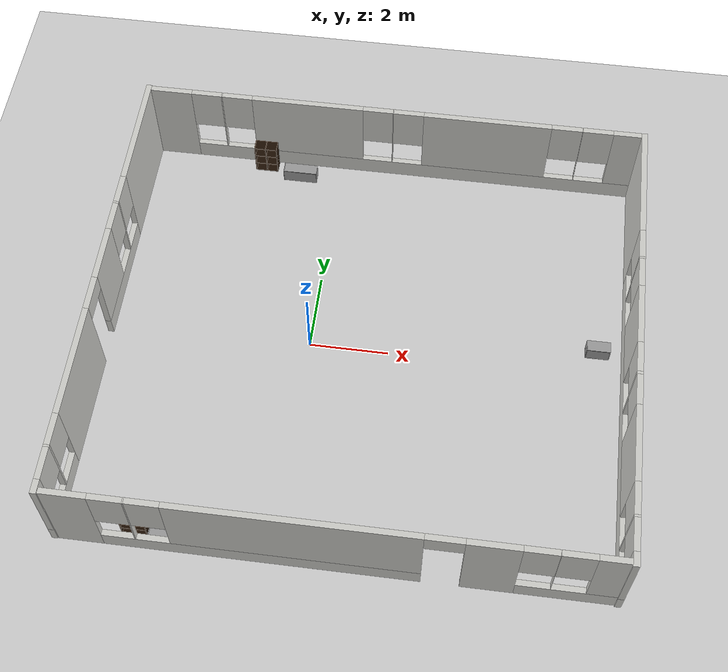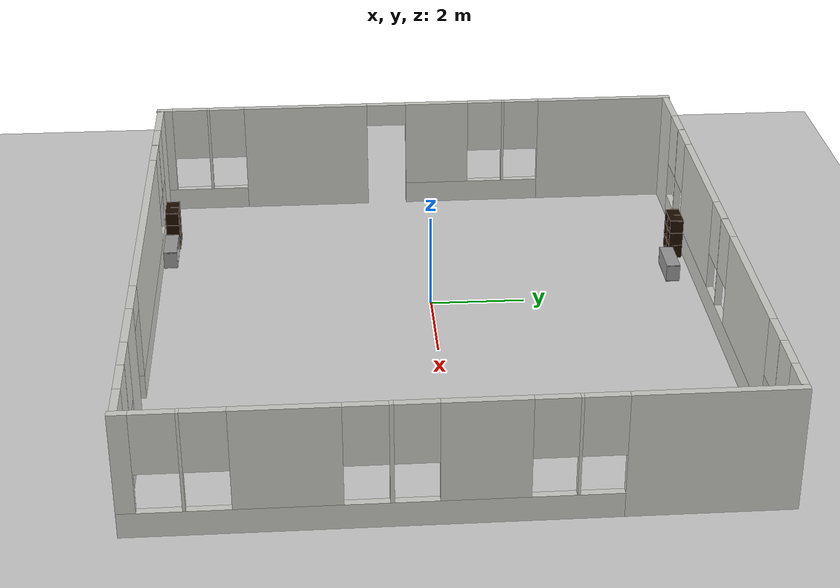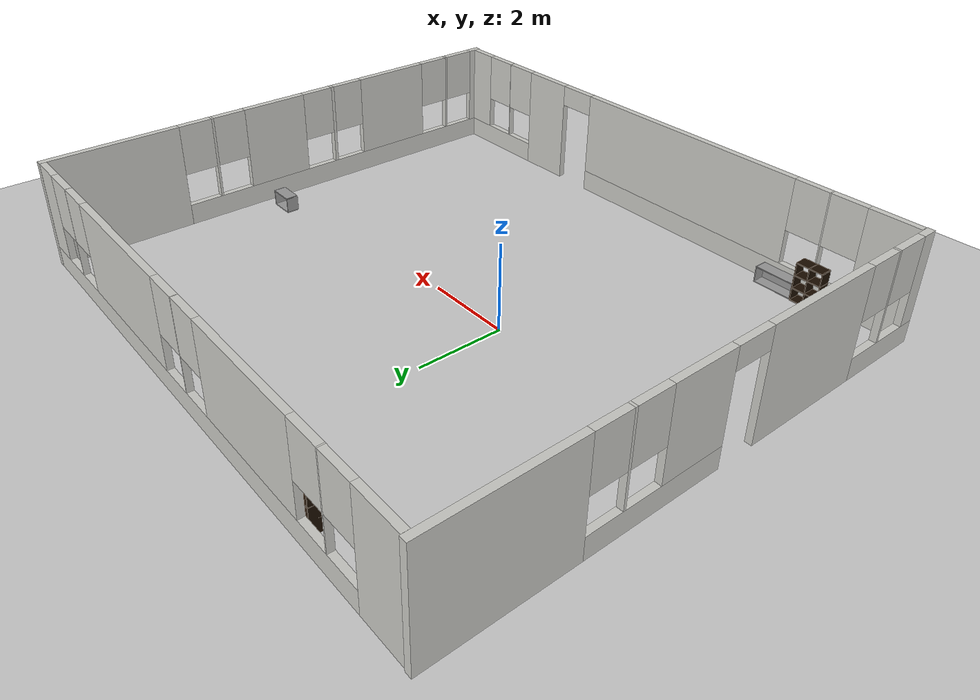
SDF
<sdf version="1.6">
 <world name="default">
  <light name="sun" type="directional">
   <pose>0 0 10 0 -0 0</pose>
   <diffuse>0.8 0.8 0.8 1</diffuse>
   <specular>0.2 0.2 0.2 1</specular>
   <attenuation>
    <range>1000</range>
    <constant>0.9</constant>
    <linear>0.01</linear>
    <quadratic>0.001</quadratic>
   </attenuation>
   <direction>-0.5 0.1 -0.9</direction>
  </light>
  <model name="ground_plane">
   <static>1</static>
   <link name="link">
    <collision name="collision">
     <geometry><plane><normal>0 0 1</normal><size>100 100</size></plane></geometry>
     <surface><friction><ode><mu>100</mu><mu2>50</mu2></ode></friction></surface>
    </collision>
    <visual name="visual">
     <cast_shadows>0</cast_shadows>
     <geometry><plane><normal>0 0 1</normal><size>100 100</size></plane></geometry>
     <material>
      <script><uri>file://media/materials/scripts/gazebo.material</uri><name>Gazebo/Grey</name></script>
     </material>
    </visual>
   </link>
  </model>
  <gravity>0 0 -9.8</gravity>
  <magnetic_field>6e-06 2.3e-05 -4.2e-05</magnetic_field>
  <atmosphere type="adiabatic"/>
  <physics name="default_physics" default="0" type="ode">
   <max_step_size>0.001</max_step_size>
   <real_time_factor>1</real_time_factor>
   <real_time_update_rate>1000</real_time_update_rate>
  </physics>
  <scene><ambient>0.4 0.4 0.4 1</ambient><background>0.7 0.7 0.7 1</background><shadows>1</shadows></scene>
  <spherical_coordinates>
   <surface_model>EARTH_WGS84</surface_model>
   <latitude_deg>0</latitude_deg>
   <longitude_deg>0</longitude_deg>
   <elevation>0</elevation>
   <heading_deg>0</heading_deg>
  </spherical_coordinates>
  <model name="wall_short_window_door_tiles">
   <pose>-5.1617 -0.004721 0 0 -0 0</pose>
   <link name="Wall_0">
    <pose>0 -0 0 0 -0 -1.5708</pose>
    <visual name="Wall_0_Visual_0">
     <pose>-4.43927 0 1.25 0 -0 0</pose>
     <geometry><box><size>3.12146 0.15 2.5</size></box></geometry>
     <material>
      <script><uri>file://media/materials/scripts/gazebo.material</uri><name>Gazebo/CeilingTiled</name></script>
      <ambient>1 1 1 1</ambient>
     </material>
     <meta><layer>0</layer></meta>
    </visual>
    <collision name="Wall_0_Collision_0">
     <geometry><box><size>3.12146 0.15 2.5</size></box></geometry>
     <pose>-4.43927 0 1.25 0 -0 0</pose>
    </collision>
    <visual name="Wall_0_Visual_1">
     <pose>2.5658 0 1.25 0 -0 0</pose>
     <geometry><box><size>2.8509 0.15 2.5</size></box></geometry>
     <material>
      <script><uri>file://media/materials/scripts/gazebo.material</uri><name>Gazebo/CeilingTiled</name></script>
      <ambient>1 1 1 1</ambient>
     </material>
     <meta><layer>0</layer></meta>
    </visual>
    <collision name="Wall_0_Collision_1">
     <geometry><box><size>2.8509 0.15 2.5</size></box></geometry>
     <pose>2.5658 0 1.25 0 -0 0</pose>
    </collision>
    <visual name="Wall_0_Visual_2">
     <pose>-1.31909 0 0.25 0 -0 0</pose>
     <geometry><box><size>3.11889 0.15 0.5</size></box></geometry>
     <material>
      <script><uri>file://media/materials/scripts/gazebo.material</uri><name>Gazebo/CeilingTiled</name></script>
      <ambient>1 1 1 1</ambient>
     </material>
     <meta><layer>0</layer></meta>
    </visual>
    <collision name="Wall_0_Collision_2">
     <geometry><box><size>3.11889 0.15 0.5</size></box></geometry>
     <pose>-1.31909 0 0.25 0 -0 0</pose>
    </collision>
    <visual name="Wall_0_Visual_3">
     <pose>4.99563 0 0.25 0 -0 0</pose>
     <geometry><box><size>2.00875 0.15 0.5</size></box></geometry>
     <material>
      <script><uri>file://media/materials/scripts/gazebo.material</uri><name>Gazebo/CeilingTiled</name></script>
      <ambient>1 1 1 1</ambient>
     </material>
     <meta><layer>0</layer></meta>
    </visual>
    <collision name="Wall_0_Collision_3">
     <geometry><box><size>2.00875 0.15 0.5</size></box></geometry>
     <pose>4.99563 0 0.25 0 -0 0</pose>
    </collision>
    <visual name="Wall_0_Visual_4">
     <pose>-2.05062 0 1.5 0 -0 0</pose>
     <geometry><box><size>0.055833 0.15 2</size></box></geometry>
     <material>
      <script><uri>file://media/materials/scripts/gazebo.material</uri><name>Gazebo/CeilingTiled</name></script>
      <ambient>1 1 1 1</ambient>
     </material>
     <meta><layer>0</layer></meta>
    </visual>
    <collision name="Wall_0_Collision_4">
     <geometry><box><size>0.055833 0.15 2</size></box></geometry>
     <pose>-2.05062 0 1.5 0 -0 0</pose>
    </collision>
    <visual name="Wall_0_Visual_5">
     <pose>-0.491177 0 1.5 0 -0 0</pose>
     <geometry><box><size>1.46306 0.15 2</size></box></geometry>
     <material>
      <script><uri>file://media/materials/scripts/gazebo.material</uri><name>Gazebo/CeilingTiled</name></script>
      <ambient>1 1 1 1</ambient>
     </material>
     <meta><layer>0</layer></meta>
    </visual>
    <collision name="Wall_0_Collision_5">
     <geometry><box><size>1.46306 0.15 2</size></box></geometry>
     <pose>-0.491177 0 1.5 0 -0 0</pose>
    </collision>
    <visual name="Wall_0_Visual_6">
     <pose>-0.491177 0 1.5 0 -0 0</pose>
     <geometry><box><size>1.46306 0.15 2</size></box></geometry>
     <material>
      <script><uri>file://media/materials/scripts/gazebo.material</uri><name>Gazebo/CeilingTiled</name></script>
      <ambient>1 1 1 1</ambient>
     </material>
     <meta><layer>0</layer></meta>
    </visual>
    <collision name="Wall_0_Collision_6">
     <geometry><box><size>1.46306 0.15 2</size></box></geometry>
     <pose>-0.491177 0 1.5 0 -0 0</pose>
    </collision>
    <visual name="Wall_0_Visual_7">
     <pose>4.81917 0 1.5 0 -0 0</pose>
     <geometry><box><size>0.055833 0.15 2</size></box></geometry>
     <material>
      <script><uri>file://media/materials/scripts/gazebo.material</uri><name>Gazebo/CeilingTiled</name></script>
      <ambient>1 1 1 1</ambient>
     </material>
     <meta><layer>0</layer></meta>
    </visual>
    <collision name="Wall_0_Collision_7">
     <geometry><box><size>0.055833 0.15 2</size></box></geometry>
     <pose>4.81917 0 1.5 0 -0 0</pose>
    </collision>
    <visual name="Wall_0_Visual_8">
     <pose>5.82354 0 1.5 0 -0 0</pose>
     <geometry><box><size>0.352917 0.15 2</size></box></geometry>
     <material>
      <script><uri>file://media/materials/scripts/gazebo.material</uri><name>Gazebo/CeilingTiled</name></script>
      <ambient>1 1 1 1</ambient>
     </material>
     <meta><layer>0</layer></meta>
    </visual>
    <collision name="Wall_0_Collision_8">
     <geometry><box><size>0.352917 0.15 2</size></box></geometry>
     <pose>5.82354 0 1.5 0 -0 0</pose>
    </collision>
    <visual name="Wall_0_Visual_9">
     <pose>-2.47854 0 1.9 0 -0 0</pose>
     <geometry><box><size>0.8 0.15 1.2</size></box></geometry>
     <material>
      <script><uri>file://media/materials/scripts/gazebo.material</uri><name>Gazebo/CeilingTiled</name></script>
      <ambient>1 1 1 1</ambient>
     </material>
     <meta><layer>0</layer></meta>
    </visual>
    <collision name="Wall_0_Collision_9">
     <geometry><box><size>0.8 0.15 1.2</size></box></geometry>
     <pose>-2.47854 0 1.9 0 -0 0</pose>
    </collision>
    <visual name="Wall_0_Visual_10">
     <pose>4.39125 0 1.9 0 -0 0</pose>
     <geometry><box><size>0.8 0.15 1.2</size></box></geometry>
     <material>
      <script><uri>file://media/materials/scripts/gazebo.material</uri><name>Gazebo/CeilingTiled</name></script>
      <ambient>1 1 1 1</ambient>
     </material>
     <meta><layer>0</layer></meta>
    </visual>
    <collision name="Wall_0_Collision_10">
     <geometry><box><size>0.8 0.15 1.2</size></box></geometry>
     <pose>4.39125 0 1.9 0 -0 0</pose>
    </collision>
    <visual name="Wall_0_Visual_11">
     <pose>-1.62271 0 1.9 0 -0 0</pose>
     <geometry><box><size>0.8 0.15 1.2</size></box></geometry>
     <material>
      <script><uri>file://media/materials/scripts/gazebo.material</uri><name>Gazebo/CeilingTiled</name></script>
      <ambient>1 1 1 1</ambient>
     </material>
     <meta><layer>0</layer></meta>
    </visual>
    <collision name="Wall_0_Collision_11">
     <geometry><box><size>0.8 0.15 1.2</size></box></geometry>
     <pose>-1.62271 0 1.9 0 -0 0</pose>
    </collision>
    <visual name="Wall_0_Visual_12">
     <pose>5.24708 0 1.9 0 -0 0</pose>
     <geometry><box><size>0.8 0.15 1.2</size></box></geometry>
     <material>
      <script><uri>file://media/materials/scripts/gazebo.material</uri><name>Gazebo/CeilingTiled</name></script>
      <ambient>1 1 1 1</ambient>
     </material>
     <meta><layer>0</layer></meta>
    </visual>
    <collision name="Wall_0_Collision_12">
     <geometry><box><size>0.8 0.15 1.2</size></box></geometry>
     <pose>5.24708 0 1.9 0 -0 0</pose>
    </collision>
    <visual name="Wall_0_Visual_13">
     <pose>0.690354 0 2.25 0 -0 0</pose>
     <geometry><box><size>0.9 0.15 0.5</size></box></geometry>
     <material>
      <script><uri>file://media/materials/scripts/gazebo.material</uri><name>Gazebo/CeilingTiled</name></script>
      <ambient>1 1 1 1</ambient>
     </material>
     <meta><layer>0</layer></meta>
    </visual>
    <collision name="Wall_0_Collision_13">
     <geometry><box><size>0.9 0.15 0.5</size></box></geometry>
     <pose>0.690354 0 2.25 0 -0 0</pose>
    </collision>
    <visual name="Wall_0_Visual_14">
     <pose>0.690354 0 2.25 0 -0 0</pose>
     <geometry><box><size>0.9 0.15 0.5</size></box></geometry>
     <material>
      <script><uri>file://media/materials/scripts/gazebo.material</uri><name>Gazebo/CeilingTiled</name></script>
      <ambient>1 1 1 1</ambient>
     </material>
     <meta><layer>0</layer></meta>
    </visual>
    <collision name="Wall_0_Collision_14">
     <geometry><box><size>0.9 0.15 0.5</size></box></geometry>
     <pose>0.690354 0 2.25 0 -0 0</pose>
    </collision>
   </link>
   <static>1</static>
  </model>
  <model name="wall_window_door_tiles">
   <pose>1.42377 -5.91503 0 0 -0 0</pose>
   <link name="Wall_0">
    <visual name="Wall_0_Visual_0">
     <pose>-5.9525 0 1.25 0 -0 0</pose>
     <geometry><box><size>1.095 0.15 2.5</size></box></geometry>
     <material>
      <script><uri>file://media/materials/scripts/gazebo.material</uri><name>Gazebo/CeilingTiled</name></script>
      <ambient>1 1 1 1</ambient>
     </material>
     <meta><layer>0</layer></meta>
    </visual>
    <collision name="Wall_0_Collision_0">
     <geometry><box><size>1.095 0.15 2.5</size></box></geometry>
     <pose>-5.9525 0 1.25 0 -0 0</pose>
    </collision>
    <visual name="Wall_0_Visual_1">
     <pose>3.555 0 1.25 0 -0 0</pose>
     <geometry><box><size>1.24 0.15 2.5</size></box></geometry>
     <material>
      <script><uri>file://media/materials/scripts/gazebo.material</uri><name>Gazebo/CeilingTiled</name></script>
      <ambient>1 1 1 1</ambient>
     </material>
     <meta><layer>0</layer></meta>
    </visual>
    <collision name="Wall_0_Collision_1">
     <geometry><box><size>1.24 0.15 2.5</size></box></geometry>
     <pose>3.555 0 1.25 0 -0 0</pose>
    </collision>
    <visual name="Wall_0_Visual_2">
     <pose>-1.685 0 0.25 0 -0 0</pose>
     <geometry><box><size>7.44 0.15 0.5</size></box></geometry>
     <material>
      <script><uri>file://media/materials/scripts/gazebo.material</uri><name>Gazebo/CeilingTiled</name></script>
      <ambient>1 1 1 1</ambient>
     </material>
     <meta><layer>0</layer></meta>
    </visual>
    <collision name="Wall_0_Collision_2">
     <geometry><box><size>7.44 0.15 0.5</size></box></geometry>
     <pose>-1.685 0 0.25 0 -0 0</pose>
    </collision>
    <visual name="Wall_0_Visual_3">
     <pose>5.3375 0 0.25 0 -0 0</pose>
     <geometry><box><size>2.325 0.15 0.5</size></box></geometry>
     <material>
      <script><uri>file://media/materials/scripts/gazebo.material</uri><name>Gazebo/CeilingTiled</name></script>
      <ambient>1 1 1 1</ambient>
     </material>
     <meta><layer>0</layer></meta>
    </visual>
    <collision name="Wall_0_Collision_3">
     <geometry><box><size>2.325 0.15 0.5</size></box></geometry>
     <pose>5.3375 0 0.25 0 -0 0</pose>
    </collision>
    <visual name="Wall_0_Visual_4">
     <pose>-4.59 0 1.5 0 -0 0</pose>
     <geometry><box><size>0.03 0.15 2</size></box></geometry>
     <material>
      <script><uri>file://media/materials/scripts/gazebo.material</uri><name>Gazebo/CeilingTiled</name></script>
      <ambient>1 1 1 1</ambient>
     </material>
     <meta><layer>0</layer></meta>
    </visual>
    <collision name="Wall_0_Collision_4">
     <geometry><box><size>0.03 0.15 2</size></box></geometry>
     <pose>-4.59 0 1.5 0 -0 0</pose>
    </collision>
    <visual name="Wall_0_Visual_5">
     <pose>-0.87 0 1.5 0 -0 0</pose>
     <geometry><box><size>5.81 0.15 2</size></box></geometry>
     <material>
      <script><uri>file://media/materials/scripts/gazebo.material</uri><name>Gazebo/CeilingTiled</name></script>
      <ambient>1 1 1 1</ambient>
     </material>
     <meta><layer>0</layer></meta>
    </visual>
    <collision name="Wall_0_Collision_5">
     <geometry><box><size>5.81 0.15 2</size></box></geometry>
     <pose>-0.87 0 1.5 0 -0 0</pose>
    </collision>
    <visual name="Wall_0_Visual_6">
     <pose>-0.87 0 1.5 0 -0 0</pose>
     <geometry><box><size>5.81 0.15 2</size></box></geometry>
     <material>
      <script><uri>file://media/materials/scripts/gazebo.material</uri><name>Gazebo/CeilingTiled</name></script>
      <ambient>1 1 1 1</ambient>
     </material>
     <meta><layer>0</layer></meta>
    </visual>
    <collision name="Wall_0_Collision_6">
     <geometry><box><size>5.81 0.15 2</size></box></geometry>
     <pose>-0.87 0 1.5 0 -0 0</pose>
    </collision>
    <visual name="Wall_0_Visual_7">
     <pose>4.98 0 1.5 0 -0 0</pose>
     <geometry><box><size>0.01 0.15 2</size></box></geometry>
     <material>
      <script><uri>file://media/materials/scripts/gazebo.material</uri><name>Gazebo/CeilingTiled</name></script>
      <ambient>1 1 1 1</ambient>
     </material>
     <meta><layer>0</layer></meta>
    </visual>
    <collision name="Wall_0_Collision_7">
     <geometry><box><size>0.01 0.15 2</size></box></geometry>
     <pose>4.98 0 1.5 0 -0 0</pose>
    </collision>
    <visual name="Wall_0_Visual_8">
     <pose>6.1425 0 1.5 0 -0 0</pose>
     <geometry><box><size>0.715 0.15 2</size></box></geometry>
     <material>
      <script><uri>file://media/materials/scripts/gazebo.material</uri><name>Gazebo/CeilingTiled</name></script>
      <ambient>1 1 1 1</ambient>
     </material>
     <meta><layer>0</layer></meta>
    </visual>
    <collision name="Wall_0_Collision_8">
     <geometry><box><size>0.715 0.15 2</size></box></geometry>
     <pose>6.1425 0 1.5 0 -0 0</pose>
    </collision>
    <visual name="Wall_0_Visual_9">
     <pose>-5.005 0 1.9 0 -0 0</pose>
     <geometry><box><size>0.8 0.15 1.2</size></box></geometry>
     <material>
      <script><uri>file://media/materials/scripts/gazebo.material</uri><name>Gazebo/CeilingTiled</name></script>
      <ambient>1 1 1 1</ambient>
     </material>
     <meta><layer>0</layer></meta>
    </visual>
    <collision name="Wall_0_Collision_9">
     <geometry><box><size>0.8 0.15 1.2</size></box></geometry>
     <pose>-5.005 0 1.9 0 -0 0</pose>
    </collision>
    <visual name="Wall_0_Visual_10">
     <pose>4.575 0 1.9 0 -0 0</pose>
     <geometry><box><size>0.8 0.15 1.2</size></box></geometry>
     <material>
      <script><uri>file://media/materials/scripts/gazebo.material</uri><name>Gazebo/CeilingTiled</name></script>
      <ambient>1 1 1 1</ambient>
     </material>
     <meta><layer>0</layer></meta>
    </visual>
    <collision name="Wall_0_Collision_10">
     <geometry><box><size>0.8 0.15 1.2</size></box></geometry>
     <pose>4.575 0 1.9 0 -0 0</pose>
    </collision>
    <visual name="Wall_0_Visual_11">
     <pose>-4.175 0 1.9 0 -0 0</pose>
     <geometry><box><size>0.8 0.15 1.2</size></box></geometry>
     <material>
      <script><uri>file://media/materials/scripts/gazebo.material</uri><name>Gazebo/CeilingTiled</name></script>
      <ambient>1 1 1 1</ambient>
     </material>
     <meta><layer>0</layer></meta>
    </visual>
    <collision name="Wall_0_Collision_11">
     <geometry><box><size>0.8 0.15 1.2</size></box></geometry>
     <pose>-4.175 0 1.9 0 -0 0</pose>
    </collision>
    <visual name="Wall_0_Visual_12">
     <pose>5.385 0 1.9 0 -0 0</pose>
     <geometry><box><size>0.8 0.15 1.2</size></box></geometry>
     <material>
      <script><uri>file://media/materials/scripts/gazebo.material</uri><name>Gazebo/CeilingTiled</name></script>
      <ambient>1 1 1 1</ambient>
     </material>
     <meta><layer>0</layer></meta>
    </visual>
    <collision name="Wall_0_Collision_12">
     <geometry><box><size>0.8 0.15 1.2</size></box></geometry>
     <pose>5.385 0 1.9 0 -0 0</pose>
    </collision>
    <visual name="Wall_0_Visual_13">
     <pose>2.485 0 2.25 0 -0 0</pose>
     <geometry><box><size>0.9 0.15 0.5</size></box></geometry>
     <material>
      <script><uri>file://media/materials/scripts/gazebo.material</uri><name>Gazebo/CeilingTiled</name></script>
      <ambient>1 1 1 1</ambient>
     </material>
     <meta><layer>0</layer></meta>
    </visual>
    <collision name="Wall_0_Collision_13">
     <geometry><box><size>0.9 0.15 0.5</size></box></geometry>
     <pose>2.485 0 2.25 0 -0 0</pose>
    </collision>
    <visual name="Wall_0_Visual_14">
     <pose>2.485 0 2.25 0 -0 0</pose>
     <geometry><box><size>0.9 0.15 0.5</size></box></geometry>
     <material>
      <script><uri>file://media/materials/scripts/gazebo.material</uri><name>Gazebo/CeilingTiled</name></script>
      <ambient>1 1 1 1</ambient>
     </material>
     <meta><layer>0</layer></meta>
    </visual>
    <collision name="Wall_0_Collision_14">
     <geometry><box><size>0.9 0.15 0.5</size></box></geometry>
     <pose>2.485 0 2.25 0 -0 0</pose>
    </collision>
   </link>
   <static>1</static>
  </model>
  <model name="wall_window_tiles">
   <pose>1.41579 5.89691 0 0 -0 0</pose>
   <link name="Wall_0">
    <visual name="Wall_0_Visual_0">
     <pose>-5.9525 0 1.25 0 -0 0</pose>
     <geometry><box><size>1.095 0.15 2.5</size></box></geometry>
     <material>
      <script><uri>file://media/materials/scripts/gazebo.material</uri><name>Gazebo/CeilingTiled</name></script>
      <ambient>1 1 1 1</ambient>
     </material>
     <meta><layer>0</layer></meta>
    </visual>
    <collision name="Wall_0_Collision_0">
     <geometry><box><size>1.095 0.15 2.5</size></box></geometry>
     <pose>-5.9525 0 1.25 0 -0 0</pose>
    </collision>
    <visual name="Wall_0_Visual_1">
     <pose>0.5475 0 0.25 0 -0 0</pose>
     <geometry><box><size>11.905 0.15 0.5</size></box></geometry>
     <material>
      <script><uri>file://media/materials/scripts/gazebo.material</uri><name>Gazebo/CeilingTiled</name></script>
      <ambient>1 1 1 1</ambient>
     </material>
     <meta><layer>0</layer></meta>
    </visual>
    <collision name="Wall_0_Collision_1">
     <geometry><box><size>11.905 0.15 0.5</size></box></geometry>
     <pose>0.5475 0 0.25 0 -0 0</pose>
    </collision>
    <visual name="Wall_0_Visual_2">
     <pose>-4.59 0 1.5 0 -0 0</pose>
     <geometry><box><size>0.03 0.15 2</size></box></geometry>
     <material>
      <script><uri>file://media/materials/scripts/gazebo.material</uri><name>Gazebo/CeilingTiled</name></script>
      <ambient>1 1 1 1</ambient>
     </material>
     <meta><layer>0</layer></meta>
    </visual>
    <collision name="Wall_0_Collision_2">
     <geometry><box><size>0.03 0.15 2</size></box></geometry>
     <pose>-4.59 0 1.5 0 -0 0</pose>
    </collision>
    <visual name="Wall_0_Visual_3">
     <pose>-2.28975 0 1.5 0 -0 0</pose>
     <geometry><box><size>2.9705 0.15 2</size></box></geometry>
     <material>
      <script><uri>file://media/materials/scripts/gazebo.material</uri><name>Gazebo/CeilingTiled</name></script>
      <ambient>1 1 1 1</ambient>
     </material>
     <meta><layer>0</layer></meta>
    </visual>
    <collision name="Wall_0_Collision_3">
     <geometry><box><size>2.9705 0.15 2</size></box></geometry>
     <pose>-2.28975 0 1.5 0 -0 0</pose>
    </collision>
    <visual name="Wall_0_Visual_4">
     <pose>0.00375 0 1.5 0 -0 0</pose>
     <geometry><box><size>0.0165 0.15 2</size></box></geometry>
     <material>
      <script><uri>file://media/materials/scripts/gazebo.material</uri><name>Gazebo/CeilingTiled</name></script>
      <ambient>1 1 1 1</ambient>
     </material>
     <meta><layer>0</layer></meta>
    </visual>
    <collision name="Wall_0_Collision_4">
     <geometry><box><size>0.0165 0.15 2</size></box></geometry>
     <pose>0.00375 0 1.5 0 -0 0</pose>
    </collision>
    <visual name="Wall_0_Visual_5">
     <pose>2.4935 0 1.5 0 -0 0</pose>
     <geometry><box><size>3.363 0.15 2</size></box></geometry>
     <material>
      <script><uri>file://media/materials/scripts/gazebo.material</uri><name>Gazebo/CeilingTiled</name></script>
      <ambient>1 1 1 1</ambient>
     </material>
     <meta><layer>0</layer></meta>
    </visual>
    <collision name="Wall_0_Collision_5">
     <geometry><box><size>3.363 0.15 2</size></box></geometry>
     <pose>2.4935 0 1.5 0 -0 0</pose>
    </collision>
    <visual name="Wall_0_Visual_6">
     <pose>4.98 0 1.5 0 -0 0</pose>
     <geometry><box><size>0.01 0.15 2</size></box></geometry>
     <material>
      <script><uri>file://media/materials/scripts/gazebo.material</uri><name>Gazebo/CeilingTiled</name></script>
      <ambient>1 1 1 1</ambient>
     </material>
     <meta><layer>0</layer></meta>
    </visual>
    <collision name="Wall_0_Collision_6">
     <geometry><box><size>0.01 0.15 2</size></box></geometry>
     <pose>4.98 0 1.5 0 -0 0</pose>
    </collision>
    <visual name="Wall_0_Visual_7">
     <pose>6.1425 0 1.5 0 -0 0</pose>
     <geometry><box><size>0.715 0.15 2</size></box></geometry>
     <material>
      <script><uri>file://media/materials/scripts/gazebo.material</uri><name>Gazebo/CeilingTiled</name></script>
      <ambient>1 1 1 1</ambient>
     </material>
     <meta><layer>0</layer></meta>
    </visual>
    <collision name="Wall_0_Collision_7">
     <geometry><box><size>0.715 0.15 2</size></box></geometry>
     <pose>6.1425 0 1.5 0 -0 0</pose>
    </collision>
    <visual name="Wall_0_Visual_8">
     <pose>-5.005 0 1.9 0 -0 0</pose>
     <geometry><box><size>0.8 0.15 1.2</size></box></geometry>
     <material>
      <script><uri>file://media/materials/scripts/gazebo.material</uri><name>Gazebo/CeilingTiled</name></script>
      <ambient>1 1 1 1</ambient>
     </material>
     <meta><layer>0</layer></meta>
    </visual>
    <collision name="Wall_0_Collision_8">
     <geometry><box><size>0.8 0.15 1.2</size></box></geometry>
     <pose>-5.005 0 1.9 0 -0 0</pose>
    </collision>
    <visual name="Wall_0_Visual_9">
     <pose>-4.175 0 1.9 0 -0 0</pose>
     <geometry><box><size>0.8 0.15 1.2</size></box></geometry>
     <material>
      <script><uri>file://media/materials/scripts/gazebo.material</uri><name>Gazebo/CeilingTiled</name></script>
      <ambient>1 1 1 1</ambient>
     </material>
     <meta><layer>0</layer></meta>
    </visual>
    <collision name="Wall_0_Collision_9">
     <geometry><box><size>0.8 0.15 1.2</size></box></geometry>
     <pose>-4.175 0 1.9 0 -0 0</pose>
    </collision>
    <visual name="Wall_0_Visual_10">
     <pose>-0.4045 0 1.9 0 -0 0</pose>
     <geometry><box><size>0.8 0.15 1.2</size></box></geometry>
     <material>
      <script><uri>file://media/materials/scripts/gazebo.material</uri><name>Gazebo/CeilingTiled</name></script>
      <ambient>1 1 1 1</ambient>
     </material>
     <meta><layer>0</layer></meta>
    </visual>
    <collision name="Wall_0_Collision_10">
     <geometry><box><size>0.8 0.15 1.2</size></box></geometry>
     <pose>-0.4045 0 1.9 0 -0 0</pose>
    </collision>
    <visual name="Wall_0_Visual_11">
     <pose>0.412 0 1.9 0 -0 0</pose>
     <geometry><box><size>0.8 0.15 1.2</size></box></geometry>
     <material>
      <script><uri>file://media/materials/scripts/gazebo.material</uri><name>Gazebo/CeilingTiled</name></script>
      <ambient>1 1 1 1</ambient>
     </material>
     <meta><layer>0</layer></meta>
    </visual>
    <collision name="Wall_0_Collision_11">
     <geometry><box><size>0.8 0.15 1.2</size></box></geometry>
     <pose>0.412 0 1.9 0 -0 0</pose>
    </collision>
    <visual name="Wall_0_Visual_12">
     <pose>4.575 0 1.9 0 -0 0</pose>
     <geometry><box><size>0.8 0.15 1.2</size></box></geometry>
     <material>
      <script><uri>file://media/materials/scripts/gazebo.material</uri><name>Gazebo/CeilingTiled</name></script>
      <ambient>1 1 1 1</ambient>
     </material>
     <meta><layer>0</layer></meta>
    </visual>
    <collision name="Wall_0_Collision_12">
     <geometry><box><size>0.8 0.15 1.2</size></box></geometry>
     <pose>4.575 0 1.9 0 -0 0</pose>
    </collision>
    <visual name="Wall_0_Visual_13">
     <pose>5.385 0 1.9 0 -0 0</pose>
     <geometry><box><size>0.8 0.15 1.2</size></box></geometry>
     <material>
      <script><uri>file://media/materials/scripts/gazebo.material</uri><name>Gazebo/CeilingTiled</name></script>
      <ambient>1 1 1 1</ambient>
     </material>
     <meta><layer>0</layer></meta>
    </visual>
    <collision name="Wall_0_Collision_13">
     <geometry><box><size>0.8 0.15 1.2</size></box></geometry>
     <pose>5.385 0 1.9 0 -0 0</pose>
    </collision>
   </link>
   <static>1</static>
  </model>
  <model name="wall_short_window_tiles">
   <pose>7.99601 -0.02569 0 0 -0 0</pose>
   <link name="Wall_0">
    <pose>0 -0 0 0 -0 -1.5708</pose>
    <visual name="Wall_0_Visual_0">
     <pose>-4.43927 0 1.25 0 -0 0</pose>
     <geometry><box><size>3.12146 0.15 2.5</size></box></geometry>
     <material>
      <script><uri>file://media/materials/scripts/gazebo.material</uri><name>Gazebo/CeilingTiled</name></script>
      <ambient>1 1 1 1</ambient>
     </material>
     <meta><layer>0</layer></meta>
    </visual>
    <collision name="Wall_0_Collision_0">
     <geometry><box><size>3.12146 0.15 2.5</size></box></geometry>
     <pose>-4.43927 0 1.25 0 -0 0</pose>
    </collision>
    <visual name="Wall_0_Visual_1">
     <pose>1.56073 0 0.25 0 -0 0</pose>
     <geometry><box><size>8.87854 0.15 0.5</size></box></geometry>
     <material>
      <script><uri>file://media/materials/scripts/gazebo.material</uri><name>Gazebo/CeilingTiled</name></script>
      <ambient>1 1 1 1</ambient>
     </material>
     <meta><layer>0</layer></meta>
    </visual>
    <collision name="Wall_0_Collision_1">
     <geometry><box><size>8.87854 0.15 0.5</size></box></geometry>
     <pose>1.56073 0 0.25 0 -0 0</pose>
    </collision>
    <visual name="Wall_0_Visual_2">
     <pose>-2.05062 0 1.5 0 -0 0</pose>
     <geometry><box><size>0.055833 0.15 2</size></box></geometry>
     <material>
      <script><uri>file://media/materials/scripts/gazebo.material</uri><name>Gazebo/CeilingTiled</name></script>
      <ambient>1 1 1 1</ambient>
     </material>
     <meta><layer>0</layer></meta>
    </visual>
    <collision name="Wall_0_Collision_2">
     <geometry><box><size>0.055833 0.15 2</size></box></geometry>
     <pose>-2.05062 0 1.5 0 -0 0</pose>
    </collision>
    <visual name="Wall_0_Visual_3">
     <pose>-0.423181 0 1.5 0 -0 0</pose>
     <geometry><box><size>1.59905 0.15 2</size></box></geometry>
     <material>
      <script><uri>file://media/materials/scripts/gazebo.material</uri><name>Gazebo/CeilingTiled</name></script>
      <ambient>1 1 1 1</ambient>
     </material>
     <meta><layer>0</layer></meta>
    </visual>
    <collision name="Wall_0_Collision_3">
     <geometry><box><size>1.59905 0.15 2</size></box></geometry>
     <pose>-0.423181 0 1.5 0 -0 0</pose>
    </collision>
    <visual name="Wall_0_Visual_4">
     <pose>1.21525 0 1.5 0 -0 0</pose>
     <geometry><box><size>0.077807 0.15 2</size></box></geometry>
     <material>
      <script><uri>file://media/materials/scripts/gazebo.material</uri><name>Gazebo/CeilingTiled</name></script>
      <ambient>1 1 1 1</ambient>
     </material>
     <meta><layer>0</layer></meta>
    </visual>
    <collision name="Wall_0_Collision_4">
     <geometry><box><size>0.077807 0.15 2</size></box></geometry>
     <pose>1.21525 0 1.5 0 -0 0</pose>
    </collision>
    <visual name="Wall_0_Visual_5">
     <pose>3.0227 0 1.5 0 -0 0</pose>
     <geometry><box><size>1.9371 0.15 2</size></box></geometry>
     <material>
      <script><uri>file://media/materials/scripts/gazebo.material</uri><name>Gazebo/CeilingTiled</name></script>
      <ambient>1 1 1 1</ambient>
     </material>
     <meta><layer>0</layer></meta>
    </visual>
    <collision name="Wall_0_Collision_5">
     <geometry><box><size>1.9371 0.15 2</size></box></geometry>
     <pose>3.0227 0 1.5 0 -0 0</pose>
    </collision>
    <visual name="Wall_0_Visual_6">
     <pose>4.81917 0 1.5 0 -0 0</pose>
     <geometry><box><size>0.055833 0.15 2</size></box></geometry>
     <material>
      <script><uri>file://media/materials/scripts/gazebo.material</uri><name>Gazebo/CeilingTiled</name></script>
      <ambient>1 1 1 1</ambient>
     </material>
     <meta><layer>0</layer></meta>
    </visual>
    <collision name="Wall_0_Collision_6">
     <geometry><box><size>0.055833 0.15 2</size></box></geometry>
     <pose>4.81917 0 1.5 0 -0 0</pose>
    </collision>
    <visual name="Wall_0_Visual_7">
     <pose>5.82354 0 1.5 0 -0 0</pose>
     <geometry><box><size>0.352917 0.15 2</size></box></geometry>
     <material>
      <script><uri>file://media/materials/scripts/gazebo.material</uri><name>Gazebo/CeilingTiled</name></script>
      <ambient>1 1 1 1</ambient>
     </material>
     <meta><layer>0</layer></meta>
    </visual>
    <collision name="Wall_0_Collision_7">
     <geometry><box><size>0.352917 0.15 2</size></box></geometry>
     <pose>5.82354 0 1.5 0 -0 0</pose>
    </collision>
    <visual name="Wall_0_Visual_8">
     <pose>-2.47854 0 1.9 0 -0 0</pose>
     <geometry><box><size>0.8 0.15 1.2</size></box></geometry>
     <material>
      <script><uri>file://media/materials/scripts/gazebo.material</uri><name>Gazebo/CeilingTiled</name></script>
      <ambient>1 1 1 1</ambient>
     </material>
     <meta><layer>0</layer></meta>
    </visual>
    <collision name="Wall_0_Collision_8">
     <geometry><box><size>0.8 0.15 1.2</size></box></geometry>
     <pose>-2.47854 0 1.9 0 -0 0</pose>
    </collision>
    <visual name="Wall_0_Visual_9">
     <pose>-1.62271 0 1.9 0 -0 0</pose>
     <geometry><box><size>0.8 0.15 1.2</size></box></geometry>
     <material>
      <script><uri>file://media/materials/scripts/gazebo.material</uri><name>Gazebo/CeilingTiled</name></script>
      <ambient>1 1 1 1</ambient>
     </material>
     <meta><layer>0</layer></meta>
    </visual>
    <collision name="Wall_0_Collision_9">
     <geometry><box><size>0.8 0.15 1.2</size></box></geometry>
     <pose>-1.62271 0 1.9 0 -0 0</pose>
    </collision>
    <visual name="Wall_0_Visual_10">
     <pose>0.776344 0 1.9 0 -0 0</pose>
     <geometry><box><size>0.8 0.15 1.2</size></box></geometry>
     <material>
      <script><uri>file://media/materials/scripts/gazebo.material</uri><name>Gazebo/CeilingTiled</name></script>
      <ambient>1 1 1 1</ambient>
     </material>
     <meta><layer>0</layer></meta>
    </visual>
    <collision name="Wall_0_Collision_10">
     <geometry><box><size>0.8 0.15 1.2</size></box></geometry>
     <pose>0.776344 0 1.9 0 -0 0</pose>
    </collision>
    <visual name="Wall_0_Visual_11">
     <pose>1.65415 0 1.9 0 -0 0</pose>
     <geometry><box><size>0.8 0.15 1.2</size></box></geometry>
     <material>
      <script><uri>file://media/materials/scripts/gazebo.material</uri><name>Gazebo/CeilingTiled</name></script>
      <ambient>1 1 1 1</ambient>
     </material>
     <meta><layer>0</layer></meta>
    </visual>
    <collision name="Wall_0_Collision_11">
     <geometry><box><size>0.8 0.15 1.2</size></box></geometry>
     <pose>1.65415 0 1.9 0 -0 0</pose>
    </collision>
    <visual name="Wall_0_Visual_12">
     <pose>4.39125 0 1.9 0 -0 0</pose>
     <geometry><box><size>0.8 0.15 1.2</size></box></geometry>
     <material>
      <script><uri>file://media/materials/scripts/gazebo.material</uri><name>Gazebo/CeilingTiled</name></script>
      <ambient>1 1 1 1</ambient>
     </material>
     <meta><layer>0</layer></meta>
    </visual>
    <collision name="Wall_0_Collision_12">
     <geometry><box><size>0.8 0.15 1.2</size></box></geometry>
     <pose>4.39125 0 1.9 0 -0 0</pose>
    </collision>
    <visual name="Wall_0_Visual_13">
     <pose>5.24708 0 1.9 0 -0 0</pose>
     <geometry><box><size>0.8 0.15 1.2</size></box></geometry>
     <material>
      <script><uri>file://media/materials/scripts/gazebo.material</uri><name>Gazebo/CeilingTiled</name></script>
      <ambient>1 1 1 1</ambient>
     </material>
     <meta><layer>0</layer></meta>
    </visual>
    <collision name="Wall_0_Collision_13">
     <geometry><box><size>0.8 0.15 1.2</size></box></geometry>
     <pose>5.24708 0 1.9 0 -0 0</pose>
    </collision>
   </link>
   <static>1</static>
  </model>
  <model name="Wall_Cabinet_36x15W_0">
   <link name="Wall_0">
    <pose>0 0 0.01 0 -0 0</pose>
    <inertial>
     <mass>1.9796</mass>
     <inertia><ixx>0.0145</ixx><iyy>0.1511</iyy><izz>0.1367</izz><ixy>0</ixy><ixz>0</ixz><iyz>0</iyz></inertia>
    </inertial>
    <collision name="Wall_0_Collision"><geometry><box><size>0.91 0.296 0.02</size></box></geometry></collision>
    <visual name="Wall_0_Visual">
     <geometry><box><size>0.91 0.296 0.02</size></box></geometry>
     <material>
      <script><uri>file://media/materials/scripts/gazebo.material</uri><name>Gazebo/Grey</name></script>
      <ambient>1 1 1 1</ambient>
     </material>
    </visual>
   </link>
   <joint name="0_2" type="fixed">
    <pose>-0.455 0 0 0 -0 0</pose>
    <parent>Wall_2</parent>
    <child>Wall_0</child>
    <axis>
     <xyz>0 0 1</xyz>
     <use_parent_model_frame>0</use_parent_model_frame>
     <limit><lower>-1e+16</lower><upper>1e+16</upper></limit>
    </axis>
   </joint>
   <joint name="0_4" type="fixed">
    <pose>0.455 0 0 0 -0 0</pose>
    <parent>Wall_4</parent>
    <child>Wall_0</child>
    <axis>
     <xyz>0 0 1</xyz>
     <use_parent_model_frame>0</use_parent_model_frame>
     <limit><lower>-1e+16</lower><upper>1e+16</upper></limit>
    </axis>
   </joint>
   <joint name="0_8" type="fixed">
    <pose>0 -0.148 0 0 -0 0</pose>
    <parent>Wall_8</parent>
    <child>Wall_0</child>
    <axis>
     <xyz>0 0 1</xyz>
     <use_parent_model_frame>0</use_parent_model_frame>
     <limit><lower>-1e+16</lower><upper>1e+16</upper></limit>
    </axis>
   </joint>
   <link name="Wall_2">
    <pose>-0.445 0 0.192 0 -0 0</pose>
    <inertial>
     <mass>0.8353</mass>
     <inertia><ixx>0.0061</ixx><iyy>0.0164</iyy><izz>0.0103</izz><ixy>0</ixy><ixz>0</ixz><iyz>0</iyz></inertia>
    </inertial>
    <collision name="Wall_2_Collision"><geometry><box><size>0.02 0.296 0.384</size></box></geometry></collision>
    <visual name="Wall_2_Visual">
     <geometry><box><size>0.02 0.296 0.384</size></box></geometry>
     <material>
      <script><uri>file://media/materials/scripts/gazebo.material</uri><name>Gazebo/Grey</name></script>
      <ambient>1 1 1 1</ambient>
     </material>
    </visual>
   </link>
   <link name="Wall_4">
    <pose>0.445 0 0.192 0 -0 0</pose>
    <inertial>
     <mass>0.8353</mass>
     <inertia><ixx>0.0061</ixx><iyy>0.0164</iyy><izz>0.0103</izz><ixy>0</ixy><ixz>0</ixz><iyz>0</iyz></inertia>
    </inertial>
    <collision name="Wall_4_Collision"><geometry><box><size>0.02 0.296 0.384</size></box></geometry></collision>
    <visual name="Wall_4_Visual">
     <geometry><box><size>0.02 0.296 0.384</size></box></geometry>
     <material>
      <script><uri>file://media/materials/scripts/gazebo.material</uri><name>Gazebo/Grey</name></script>
      <ambient>1 1 1 1</ambient>
     </material>
    </visual>
   </link>
   <link name="Wall_6">
    <pose>0 0 0.374 0 -0 0</pose>
    <inertial>
     <mass>1.9796</mass>
     <inertia><ixx>0.0145</ixx><iyy>0.1511</iyy><izz>0.1367</izz><ixy>0</ixy><ixz>0</ixz><iyz>0</iyz></inertia>
    </inertial>
    <collision name="Wall_6_Collision"><geometry><box><size>0.91 0.296 0.02</size></box></geometry></collision>
    <visual name="Wall_6_Visual">
     <geometry><box><size>0.91 0.296 0.02</size></box></geometry>
     <material>
      <script><uri>file://media/materials/scripts/gazebo.material</uri><name>Gazebo/Grey</name></script>
      <ambient>1 1 1 1</ambient>
     </material>
    </visual>
   </link>
   <joint name="6_2" type="fixed">
    <pose>-0.455 0 0 0 -0 0</pose>
    <parent>Wall_2</parent>
    <child>Wall_6</child>
    <axis>
     <xyz>0 0 1</xyz>
     <use_parent_model_frame>0</use_parent_model_frame>
     <limit><lower>-1e+16</lower><upper>1e+16</upper></limit>
    </axis>
   </joint>
   <joint name="6_4" type="fixed">
    <pose>0.455 0 0 0 -0 0</pose>
    <parent>Wall_4</parent>
    <child>Wall_6</child>
    <axis>
     <xyz>0 0 1</xyz>
     <use_parent_model_frame>0</use_parent_model_frame>
     <limit><lower>-1e+16</lower><upper>1e+16</upper></limit>
    </axis>
   </joint>
   <joint name="6_8" type="fixed">
    <pose>0 -0.148 0 0 -0 0</pose>
    <parent>Wall_8</parent>
    <child>Wall_6</child>
    <axis>
     <xyz>0 0 1</xyz>
     <use_parent_model_frame>0</use_parent_model_frame>
     <limit><lower>-1e+16</lower><upper>1e+16</upper></limit>
    </axis>
   </joint>
   <link name="Wall_8">
    <pose>0 -0.138 0.19 0 -0 0</pose>
    <inertial>
     <mass>2.5302</mass>
     <inertia><ixx>0.0305</ixx><iyy>0.1732</iyy><izz>0.2035</izz><ixy>0</ixy><ixz>0</ixz><iyz>0</iyz></inertia>
    </inertial>
    <collision name="Wall_8_Collision"><geometry><box><size>0.906 0.02 0.38</size></box></geometry></collision>
    <visual name="Wall_8_Visual">
     <geometry><box><size>0.906 0.02 0.38</size></box></geometry>
     <material>
      <script><uri>file://media/materials/scripts/gazebo.material</uri><name>Gazebo/Grey</name></script>
      <ambient>1 1 1 1</ambient>
     </material>
    </visual>
   </link>
   <joint name="8_2" type="fixed">
    <pose>-0.453 0 0 0 -0 0</pose>
    <parent>Wall_2</parent>
    <child>Wall_8</child>
    <axis>
     <xyz>0 1 0</xyz>
     <use_parent_model_frame>0</use_parent_model_frame>
     <limit><lower>-1e+16</lower><upper>1e+16</upper></limit>
    </axis>
   </joint>
   <joint name="8_4" type="fixed">
    <pose>0.453 0 0 0 -0 0</pose>
    <parent>Wall_4</parent>
    <child>Wall_8</child>
    <axis>
     <xyz>0 1 0</xyz>
     <use_parent_model_frame>0</use_parent_model_frame>
     <limit><lower>-1e+16</lower><upper>1e+16</upper></limit>
    </axis>
   </joint>
   <static>1</static>
   <pose>-2.48426 -5.67054 0 0 -0 0</pose>
  </model>
  <model name="6_Cube_StorageE">
   <link name="Wall_0">
    <pose>0 0 0.01 0 -0 0</pose>
    <inertial>
     <mass>1.6201</mass>
     <inertia><ixx>0.0119</ixx><iyy>0.0631</iyy><izz>0.0513</izz><ixy>0</ixy><ixz>0</ixz><iyz>0</iyz></inertia>
    </inertial>
    <collision name="Wall_0_Collision"><geometry><box><size>0.616 0.296 0.02</size></box></geometry></collision>
    <visual name="Wall_0_Visual">
     <geometry><box><size>0.616 0.296 0.02</size></box></geometry>
     <material>
      <script><uri>file://media/materials/scripts/gazebo.material</uri><name>Gazebo/Grey</name></script>
      <ambient>0.105882 0.0509804 0 1</ambient>
     </material>
    </visual>
   </link>
   <joint name="0_2" type="fixed">
    <pose>-0.308 0 0 0 -0 0</pose>
    <parent>Wall_2</parent>
    <child>Wall_0</child>
    <axis>
     <xyz>1 0 0</xyz>
     <use_parent_model_frame>0</use_parent_model_frame>
     <limit><lower>-1e+16</lower><upper>1e+16</upper></limit>
    </axis>
   </joint>
   <joint name="0_12" type="fixed">
    <parent>Wall_12</parent>
    <child>Wall_0</child>
    <axis>
     <xyz>0 0 1</xyz>
     <use_parent_model_frame>0</use_parent_model_frame>
     <limit><lower>-1e+16</lower><upper>1e+16</upper></limit>
    </axis>
   </joint>
   <joint name="0_4" type="fixed">
    <pose>0.308 0 0 0 -0 0</pose>
    <parent>Wall_4</parent>
    <child>Wall_0</child>
    <axis>
     <xyz>1 0 0</xyz>
     <use_parent_model_frame>0</use_parent_model_frame>
     <limit><lower>-1e+16</lower><upper>1e+16</upper></limit>
    </axis>
   </joint>
   <link name="Wall_10">
    <pose>0 0 0.61 0 -0 0</pose>
    <inertial>
     <mass>1.6201</mass>
     <inertia><ixx>0.0119</ixx><iyy>0.0631</iyy><izz>0.0513</izz><ixy>0</ixy><ixz>0</ixz><iyz>0</iyz></inertia>
    </inertial>
    <collision name="Wall_10_Collision"><geometry><box><size>0.616 0.296 0.02</size></box></geometry></collision>
    <visual name="Wall_10_Visual">
     <geometry><box><size>0.616 0.296 0.02</size></box></geometry>
     <material>
      <script><uri>file://media/materials/scripts/gazebo.material</uri><name>Gazebo/Grey</name></script>
      <ambient>0.105882 0.0509804 0 1</ambient>
     </material>
    </visual>
   </link>
   <joint name="10_2" type="fixed">
    <pose>-0.308 0 0 0 -0 0</pose>
    <parent>Wall_2</parent>
    <child>Wall_10</child>
    <axis>
     <xyz>1 0 0</xyz>
     <use_parent_model_frame>0</use_parent_model_frame>
     <limit><lower>-1e+16</lower><upper>1e+16</upper></limit>
    </axis>
   </joint>
   <joint name="10_12" type="fixed">
    <parent>Wall_12</parent>
    <child>Wall_10</child>
    <axis>
     <xyz>0 0 1</xyz>
     <use_parent_model_frame>0</use_parent_model_frame>
     <limit><lower>-1e+16</lower><upper>1e+16</upper></limit>
    </axis>
   </joint>
   <joint name="10_4" type="fixed">
    <pose>0.308 0 0 0 -0 0</pose>
    <parent>Wall_4</parent>
    <child>Wall_10</child>
    <axis>
     <xyz>1 0 0</xyz>
     <use_parent_model_frame>0</use_parent_model_frame>
     <limit><lower>-1e+16</lower><upper>1e+16</upper></limit>
    </axis>
   </joint>
   <link name="Wall_12">
    <pose>0 0 0.4575 0 -0 0</pose>
    <inertial>
     <mass>2.4065</mass>
     <inertia><ixx>0.0177</ixx><iyy>0.1855</iyy><izz>0.168</izz><ixy>0</ixy><ixz>0</ixz><iyz>0</iyz></inertia>
    </inertial>
    <collision name="Wall_12_Collision"><geometry><box><size>0.02 0.296 0.915</size></box></geometry></collision>
    <visual name="Wall_12_Visual">
     <geometry><box><size>0.02 0.296 0.915</size></box></geometry>
     <material>
      <script><uri>file://media/materials/scripts/gazebo.material</uri><name>Gazebo/Grey</name></script>
      <ambient>0.105882 0.0509804 0 1</ambient>
     </material>
    </visual>
   </link>
   <link name="Wall_2">
    <pose>-0.298 0 0.4575 0 -0 0</pose>
    <inertial>
     <mass>2.4065</mass>
     <inertia><ixx>0.0177</ixx><iyy>0.1855</iyy><izz>0.168</izz><ixy>0</ixy><ixz>0</ixz><iyz>0</iyz></inertia>
    </inertial>
    <collision name="Wall_2_Collision"><geometry><box><size>0.02 0.296 0.915</size></box></geometry></collision>
    <visual name="Wall_2_Visual">
     <geometry><box><size>0.02 0.296 0.915</size></box></geometry>
     <material>
      <script><uri>file://media/materials/scripts/gazebo.material</uri><name>Gazebo/Grey</name></script>
      <ambient>0.105882 0.0509804 0 1</ambient>
     </material>
    </visual>
   </link>
   <link name="Wall_4">
    <pose>0.298 0 0.4575 0 -0 0</pose>
    <inertial>
     <mass>2.4065</mass>
     <inertia><ixx>0.0177</ixx><iyy>0.1855</iyy><izz>0.168</izz><ixy>0</ixy><ixz>0</ixz><iyz>0</iyz></inertia>
    </inertial>
    <collision name="Wall_4_Collision"><geometry><box><size>0.02 0.296 0.915</size></box></geometry></collision>
    <visual name="Wall_4_Visual">
     <geometry><box><size>0.02 0.296 0.915</size></box></geometry>
     <material>
      <script><uri>file://media/materials/scripts/gazebo.material</uri><name>Gazebo/Grey</name></script>
      <ambient>0.105882 0.0509804 0 1</ambient>
     </material>
    </visual>
   </link>
   <link name="Wall_6">
    <pose>0 0 0.905 0 -0 0</pose>
    <inertial>
     <mass>1.6201</mass>
     <inertia><ixx>0.0119</ixx><iyy>0.0631</iyy><izz>0.0513</izz><ixy>0</ixy><ixz>0</ixz><iyz>0</iyz></inertia>
    </inertial>
    <collision name="Wall_6_Collision"><geometry><box><size>0.616 0.296 0.02</size></box></geometry></collision>
    <visual name="Wall_6_Visual">
     <geometry><box><size>0.616 0.296 0.02</size></box></geometry>
     <material>
      <script><uri>file://media/materials/scripts/gazebo.material</uri><name>Gazebo/Grey</name></script>
      <ambient>0.105882 0.0509804 0 1</ambient>
     </material>
    </visual>
   </link>
   <joint name="6_2" type="fixed">
    <pose>-0.308 0 0 0 -0 0</pose>
    <parent>Wall_2</parent>
    <child>Wall_6</child>
    <axis>
     <xyz>2 0 0</xyz>
     <use_parent_model_frame>0</use_parent_model_frame>
     <limit><lower>-1e+16</lower><upper>1e+16</upper></limit>
    </axis>
   </joint>
   <joint name="6_12" type="fixed">
    <parent>Wall_12</parent>
    <child>Wall_6</child>
    <axis>
     <xyz>0 0 1</xyz>
     <use_parent_model_frame>0</use_parent_model_frame>
     <limit><lower>-1e+16</lower><upper>1e+16</upper></limit>
    </axis>
   </joint>
   <joint name="6_4" type="fixed">
    <pose>0.308 0 0 0 -0 0</pose>
    <parent>Wall_4</parent>
    <child>Wall_6</child>
    <axis>
     <xyz>1 0 0</xyz>
     <use_parent_model_frame>0</use_parent_model_frame>
     <limit><lower>-1e+16</lower><upper>1e+16</upper></limit>
    </axis>
   </joint>
   <link name="Wall_8">
    <pose>0 0 0.305 0 -0 0</pose>
    <inertial>
     <mass>1.6201</mass>
     <inertia><ixx>0.0119</ixx><iyy>0.0631</iyy><izz>0.0513</izz><ixy>0</ixy><ixz>0</ixz><iyz>0</iyz></inertia>
    </inertial>
    <collision name="Wall_8_Collision"><geometry><box><size>0.616 0.296 0.02</size></box></geometry></collision>
    <visual name="Wall_8_Visual">
     <geometry><box><size>0.616 0.296 0.02</size></box></geometry>
     <material>
      <script><uri>file://media/materials/scripts/gazebo.material</uri><name>Gazebo/Grey</name></script>
      <ambient>0.105882 0.0509804 0 1</ambient>
     </material>
    </visual>
   </link>
   <joint name="8_2" type="fixed">
    <pose>-0.308 0 0 0 -0 0</pose>
    <parent>Wall_2</parent>
    <child>Wall_8</child>
    <axis>
     <xyz>1 0 0</xyz>
     <use_parent_model_frame>0</use_parent_model_frame>
     <limit><lower>-1e+16</lower><upper>1e+16</upper></limit>
    </axis>
   </joint>
   <joint name="8_12" type="fixed">
    <parent>Wall_12</parent>
    <child>Wall_8</child>
    <axis>
     <xyz>0 0 1</xyz>
     <use_parent_model_frame>0</use_parent_model_frame>
     <limit><lower>-1e+16</lower><upper>1e+16</upper></limit>
    </axis>
   </joint>
   <joint name="8_4" type="fixed">
    <pose>0.308 0 0 0 -0 0</pose>
    <parent>Wall_4</parent>
    <child>Wall_8</child>
    <axis>
     <xyz>1 0 0</xyz>
     <use_parent_model_frame>0</use_parent_model_frame>
     <limit><lower>-1e+16</lower><upper>1e+16</upper></limit>
    </axis>
   </joint>
   <static>1</static>
   <pose>-3.24822 -5.64839 0 0 -0 0</pose>
  </model>
  <model name="6_Cube_StorageE_0">
   <link name="Wall_0">
    <pose>0 0 0.01 0 -0 0</pose>
    <inertial>
     <mass>1.6201</mass>
     <inertia><ixx>0.0119</ixx><iyy>0.0631</iyy><izz>0.0513</izz><ixy>0</ixy><ixz>0</ixz><iyz>0</iyz></inertia>
    </inertial>
    <collision name="Wall_0_Collision"><geometry><box><size>0.616 0.296 0.02</size></box></geometry></collision>
    <visual name="Wall_0_Visual">
     <geometry><box><size>0.616 0.296 0.02</size></box></geometry>
     <material>
      <script><uri>file://media/materials/scripts/gazebo.material</uri><name>Gazebo/Grey</name></script>
      <ambient>0.105882 0.0509804 0 1</ambient>
     </material>
    </visual>
   </link>
   <joint name="0_2" type="fixed">
    <pose>-0.308 0 0 0 -0 0</pose>
    <parent>Wall_2</parent>
    <child>Wall_0</child>
    <axis>
     <xyz>1 0 0</xyz>
     <use_parent_model_frame>0</use_parent_model_frame>
     <limit><lower>-1e+16</lower><upper>1e+16</upper></limit>
    </axis>
   </joint>
   <joint name="0_12" type="fixed">
    <parent>Wall_12</parent>
    <child>Wall_0</child>
    <axis>
     <xyz>0 0 1</xyz>
     <use_parent_model_frame>0</use_parent_model_frame>
     <limit><lower>-1e+16</lower><upper>1e+16</upper></limit>
    </axis>
   </joint>
   <joint name="0_4" type="fixed">
    <pose>0.308 0 0 0 -0 0</pose>
    <parent>Wall_4</parent>
    <child>Wall_0</child>
    <axis>
     <xyz>1 0 0</xyz>
     <use_parent_model_frame>0</use_parent_model_frame>
     <limit><lower>-1e+16</lower><upper>1e+16</upper></limit>
    </axis>
   </joint>
   <link name="Wall_10">
    <pose>0 0 0.61 0 -0 0</pose>
    <inertial>
     <mass>1.6201</mass>
     <inertia><ixx>0.0119</ixx><iyy>0.0631</iyy><izz>0.0513</izz><ixy>0</ixy><ixz>0</ixz><iyz>0</iyz></inertia>
    </inertial>
    <collision name="Wall_10_Collision"><geometry><box><size>0.616 0.296 0.02</size></box></geometry></collision>
    <visual name="Wall_10_Visual">
     <geometry><box><size>0.616 0.296 0.02</size></box></geometry>
     <material>
      <script><uri>file://media/materials/scripts/gazebo.material</uri><name>Gazebo/Grey</name></script>
      <ambient>0.105882 0.0509804 0 1</ambient>
     </material>
    </visual>
   </link>
   <joint name="10_2" type="fixed">
    <pose>-0.308 0 0 0 -0 0</pose>
    <parent>Wall_2</parent>
    <child>Wall_10</child>
    <axis>
     <xyz>1 0 0</xyz>
     <use_parent_model_frame>0</use_parent_model_frame>
     <limit><lower>-1e+16</lower><upper>1e+16</upper></limit>
    </axis>
   </joint>
   <joint name="10_12" type="fixed">
    <parent>Wall_12</parent>
    <child>Wall_10</child>
    <axis>
     <xyz>0 0 1</xyz>
     <use_parent_model_frame>0</use_parent_model_frame>
     <limit><lower>-1e+16</lower><upper>1e+16</upper></limit>
    </axis>
   </joint>
   <joint name="10_4" type="fixed">
    <pose>0.308 0 0 0 -0 0</pose>
    <parent>Wall_4</parent>
    <child>Wall_10</child>
    <axis>
     <xyz>1 0 0</xyz>
     <use_parent_model_frame>0</use_parent_model_frame>
     <limit><lower>-1e+16</lower><upper>1e+16</upper></limit>
    </axis>
   </joint>
   <link name="Wall_12">
    <pose>0 0 0.4575 0 -0 0</pose>
    <inertial>
     <mass>2.4065</mass>
     <inertia><ixx>0.0177</ixx><iyy>0.1855</iyy><izz>0.168</izz><ixy>0</ixy><ixz>0</ixz><iyz>0</iyz></inertia>
    </inertial>
    <collision name="Wall_12_Collision"><geometry><box><size>0.02 0.296 0.915</size></box></geometry></collision>
    <visual name="Wall_12_Visual">
     <geometry><box><size>0.02 0.296 0.915</size></box></geometry>
     <material>
      <script><uri>file://media/materials/scripts/gazebo.material</uri><name>Gazebo/Grey</name></script>
      <ambient>0.105882 0.0509804 0 1</ambient>
     </material>
    </visual>
   </link>
   <link name="Wall_2">
    <pose>-0.298 0 0.4575 0 -0 0</pose>
    <inertial>
     <mass>2.4065</mass>
     <inertia><ixx>0.0177</ixx><iyy>0.1855</iyy><izz>0.168</izz><ixy>0</ixy><ixz>0</ixz><iyz>0</iyz></inertia>
    </inertial>
    <collision name="Wall_2_Collision"><geometry><box><size>0.02 0.296 0.915</size></box></geometry></collision>
    <visual name="Wall_2_Visual">
     <geometry><box><size>0.02 0.296 0.915</size></box></geometry>
     <material>
      <script><uri>file://media/materials/scripts/gazebo.material</uri><name>Gazebo/Grey</name></script>
      <ambient>0.105882 0.0509804 0 1</ambient>
     </material>
    </visual>
   </link>
   <link name="Wall_4">
    <pose>0.298 0 0.4575 0 -0 0</pose>
    <inertial>
     <mass>2.4065</mass>
     <inertia><ixx>0.0177</ixx><iyy>0.1855</iyy><izz>0.168</izz><ixy>0</ixy><ixz>0</ixz><iyz>0</iyz></inertia>
    </inertial>
    <collision name="Wall_4_Collision"><geometry><box><size>0.02 0.296 0.915</size></box></geometry></collision>
    <visual name="Wall_4_Visual">
     <geometry><box><size>0.02 0.296 0.915</size></box></geometry>
     <material>
      <script><uri>file://media/materials/scripts/gazebo.material</uri><name>Gazebo/Grey</name></script>
      <ambient>0.105882 0.0509804 0 1</ambient>
     </material>
    </visual>
   </link>
   <link name="Wall_6">
    <pose>0 0 0.905 0 -0 0</pose>
    <inertial>
     <mass>1.6201</mass>
     <inertia><ixx>0.0119</ixx><iyy>0.0631</iyy><izz>0.0513</izz><ixy>0</ixy><ixz>0</ixz><iyz>0</iyz></inertia>
    </inertial>
    <collision name="Wall_6_Collision"><geometry><box><size>0.616 0.296 0.02</size></box></geometry></collision>
    <visual name="Wall_6_Visual">
     <geometry><box><size>0.616 0.296 0.02</size></box></geometry>
     <material>
      <script><uri>file://media/materials/scripts/gazebo.material</uri><name>Gazebo/Grey</name></script>
      <ambient>0.105882 0.0509804 0 1</ambient>
     </material>
    </visual>
   </link>
   <joint name="6_2" type="fixed">
    <pose>-0.308 0 0 0 -0 0</pose>
    <parent>Wall_2</parent>
    <child>Wall_6</child>
    <axis>
     <xyz>2 0 0</xyz>
     <use_parent_model_frame>0</use_parent_model_frame>
     <limit><lower>-1e+16</lower><upper>1e+16</upper></limit>
    </axis>
   </joint>
   <joint name="6_12" type="fixed">
    <parent>Wall_12</parent>
    <child>Wall_6</child>
    <axis>
     <xyz>0 0 1</xyz>
     <use_parent_model_frame>0</use_parent_model_frame>
     <limit><lower>-1e+16</lower><upper>1e+16</upper></limit>
    </axis>
   </joint>
   <joint name="6_4" type="fixed">
    <pose>0.308 0 0 0 -0 0</pose>
    <parent>Wall_4</parent>
    <child>Wall_6</child>
    <axis>
     <xyz>1 0 0</xyz>
     <use_parent_model_frame>0</use_parent_model_frame>
     <limit><lower>-1e+16</lower><upper>1e+16</upper></limit>
    </axis>
   </joint>
   <link name="Wall_8">
    <pose>0 0 0.305 0 -0 0</pose>
    <inertial>
     <mass>1.6201</mass>
     <inertia><ixx>0.0119</ixx><iyy>0.0631</iyy><izz>0.0513</izz><ixy>0</ixy><ixz>0</ixz><iyz>0</iyz></inertia>
    </inertial>
    <collision name="Wall_8_Collision"><geometry><box><size>0.616 0.296 0.02</size></box></geometry></collision>
    <visual name="Wall_8_Visual">
     <geometry><box><size>0.616 0.296 0.02</size></box></geometry>
     <material>
      <script><uri>file://media/materials/scripts/gazebo.material</uri><name>Gazebo/Grey</name></script>
      <ambient>0.105882 0.0509804 0 1</ambient>
     </material>
    </visual>
   </link>
   <joint name="8_2" type="fixed">
    <pose>-0.308 0 0 0 -0 0</pose>
    <parent>Wall_2</parent>
    <child>Wall_8</child>
    <axis>
     <xyz>1 0 0</xyz>
     <use_parent_model_frame>0</use_parent_model_frame>
     <limit><lower>-1e+16</lower><upper>1e+16</upper></limit>
    </axis>
   </joint>
   <joint name="8_12" type="fixed">
    <parent>Wall_12</parent>
    <child>Wall_8</child>
    <axis>
     <xyz>0 0 1</xyz>
     <use_parent_model_frame>0</use_parent_model_frame>
     <limit><lower>-1e+16</lower><upper>1e+16</upper></limit>
    </axis>
   </joint>
   <joint name="8_4" type="fixed">
    <pose>0.308 0 0 0 -0 0</pose>
    <parent>Wall_4</parent>
    <child>Wall_8</child>
    <axis>
     <xyz>1 0 0</xyz>
     <use_parent_model_frame>0</use_parent_model_frame>
     <limit><lower>-1e+16</lower><upper>1e+16</upper></limit>
    </axis>
   </joint>
   <static>1</static>
   <pose>-2.04149 5.62712 0 0 -0 0</pose>
  </model>
  <model name="Wall_Cabinet_36x15W">
   <link name="Wall_0">
    <pose>0 0 0.01 0 -0 0</pose>
    <inertial>
     <mass>1.9796</mass>
     <inertia><ixx>0.0145</ixx><iyy>0.1511</iyy><izz>0.1367</izz><ixy>0</ixy><ixz>0</ixz><iyz>0</iyz></inertia>
    </inertial>
    <collision name="Wall_0_Collision"><geometry><box><size>0.91 0.296 0.02</size></box></geometry></collision>
    <visual name="Wall_0_Visual">
     <geometry><box><size>0.91 0.296 0.02</size></box></geometry>
     <material>
      <script><uri>file://media/materials/scripts/gazebo.material</uri><name>Gazebo/Grey</name></script>
      <ambient>1 1 1 1</ambient>
     </material>
    </visual>
   </link>
   <joint name="0_2" type="fixed">
    <pose>-0.455 0 0 0 -0 0</pose>
    <parent>Wall_2</parent>
    <child>Wall_0</child>
    <axis>
     <xyz>0 0 1</xyz>
     <use_parent_model_frame>0</use_parent_model_frame>
     <limit><lower>-1e+16</lower><upper>1e+16</upper></limit>
    </axis>
   </joint>
   <joint name="0_4" type="fixed">
    <pose>0.455 0 0 0 -0 0</pose>
    <parent>Wall_4</parent>
    <child>Wall_0</child>
    <axis>
     <xyz>0 0 1</xyz>
     <use_parent_model_frame>0</use_parent_model_frame>
     <limit><lower>-1e+16</lower><upper>1e+16</upper></limit>
    </axis>
   </joint>
   <joint name="0_8" type="fixed">
    <pose>0 -0.148 0 0 -0 0</pose>
    <parent>Wall_8</parent>
    <child>Wall_0</child>
    <axis>
     <xyz>0 0 1</xyz>
     <use_parent_model_frame>0</use_parent_model_frame>
     <limit><lower>-1e+16</lower><upper>1e+16</upper></limit>
    </axis>
   </joint>
   <link name="Wall_2">
    <pose>-0.445 0 0.192 0 -0 0</pose>
    <inertial>
     <mass>0.8353</mass>
     <inertia><ixx>0.0061</ixx><iyy>0.0164</iyy><izz>0.0103</izz><ixy>0</ixy><ixz>0</ixz><iyz>0</iyz></inertia>
    </inertial>
    <collision name="Wall_2_Collision"><geometry><box><size>0.02 0.296 0.384</size></box></geometry></collision>
    <visual name="Wall_2_Visual">
     <geometry><box><size>0.02 0.296 0.384</size></box></geometry>
     <material>
      <script><uri>file://media/materials/scripts/gazebo.material</uri><name>Gazebo/Grey</name></script>
      <ambient>1 1 1 1</ambient>
     </material>
    </visual>
   </link>
   <link name="Wall_4">
    <pose>0.445 0 0.192 0 -0 0</pose>
    <inertial>
     <mass>0.8353</mass>
     <inertia><ixx>0.0061</ixx><iyy>0.0164</iyy><izz>0.0103</izz><ixy>0</ixy><ixz>0</ixz><iyz>0</iyz></inertia>
    </inertial>
    <collision name="Wall_4_Collision"><geometry><box><size>0.02 0.296 0.384</size></box></geometry></collision>
    <visual name="Wall_4_Visual">
     <geometry><box><size>0.02 0.296 0.384</size></box></geometry>
     <material>
      <script><uri>file://media/materials/scripts/gazebo.material</uri><name>Gazebo/Grey</name></script>
      <ambient>1 1 1 1</ambient>
     </material>
    </visual>
   </link>
   <link name="Wall_6">
    <pose>0 0 0.374 0 -0 0</pose>
    <inertial>
     <mass>1.9796</mass>
     <inertia><ixx>0.0145</ixx><iyy>0.1511</iyy><izz>0.1367</izz><ixy>0</ixy><ixz>0</ixz><iyz>0</iyz></inertia>
    </inertial>
    <collision name="Wall_6_Collision"><geometry><box><size>0.91 0.296 0.02</size></box></geometry></collision>
    <visual name="Wall_6_Visual">
     <geometry><box><size>0.91 0.296 0.02</size></box></geometry>
     <material>
      <script><uri>file://media/materials/scripts/gazebo.material</uri><name>Gazebo/Grey</name></script>
      <ambient>1 1 1 1</ambient>
     </material>
    </visual>
   </link>
   <joint name="6_2" type="fixed">
    <pose>-0.455 0 0 0 -0 0</pose>
    <parent>Wall_2</parent>
    <child>Wall_6</child>
    <axis>
     <xyz>0 0 1</xyz>
     <use_parent_model_frame>0</use_parent_model_frame>
     <limit><lower>-1e+16</lower><upper>1e+16</upper></limit>
    </axis>
   </joint>
   <joint name="6_4" type="fixed">
    <pose>0.455 0 0 0 -0 0</pose>
    <parent>Wall_4</parent>
    <child>Wall_6</child>
    <axis>
     <xyz>0 0 1</xyz>
     <use_parent_model_frame>0</use_parent_model_frame>
     <limit><lower>-1e+16</lower><upper>1e+16</upper></limit>
    </axis>
   </joint>
   <joint name="6_8" type="fixed">
    <pose>0 -0.148 0 0 -0 0</pose>
    <parent>Wall_8</parent>
    <child>Wall_6</child>
    <axis>
     <xyz>0 0 1</xyz>
     <use_parent_model_frame>0</use_parent_model_frame>
     <limit><lower>-1e+16</lower><upper>1e+16</upper></limit>
    </axis>
   </joint>
   <link name="Wall_8">
    <pose>0 -0.138 0.19 0 -0 0</pose>
    <inertial>
     <mass>2.5302</mass>
     <inertia><ixx>0.0305</ixx><iyy>0.1732</iyy><izz>0.2035</izz><ixy>0</ixy><ixz>0</ixz><iyz>0</iyz></inertia>
    </inertial>
    <collision name="Wall_8_Collision"><geometry><box><size>0.906 0.02 0.38</size></box></geometry></collision>
    <visual name="Wall_8_Visual">
     <geometry><box><size>0.906 0.02 0.38</size></box></geometry>
     <material>
      <script><uri>file://media/materials/scripts/gazebo.material</uri><name>Gazebo/Grey</name></script>
      <ambient>1 1 1 1</ambient>
     </material>
    </visual>
   </link>
   <joint name="8_2" type="fixed">
    <pose>-0.453 0 0 0 -0 0</pose>
    <parent>Wall_2</parent>
    <child>Wall_8</child>
    <axis>
     <xyz>0 1 0</xyz>
     <use_parent_model_frame>0</use_parent_model_frame>
     <limit><lower>-1e+16</lower><upper>1e+16</upper></limit>
    </axis>
   </joint>
   <joint name="8_4" type="fixed">
    <pose>0.453 0 0 0 -0 0</pose>
    <parent>Wall_4</parent>
    <child>Wall_8</child>
    <axis>
     <xyz>0 1 0</xyz>
     <use_parent_model_frame>0</use_parent_model_frame>
     <limit><lower>-1e+16</lower><upper>1e+16</upper></limit>
    </axis>
   </joint>
   <static>1</static>
   <pose>-1.06804 5.36866 0 0 -0 0</pose>
  </model>
  <model name="Wall_Cabinet_24x15W">
   <link name="Wall_41">
    <pose>0 0 0.01 0 -0 0</pose>
    <inertial>
     <mass>1.4983</mass>
     <inertia><ixx>0.011</ixx><iyy>0.0571</iyy><izz>0.0462</izz><ixy>0</ixy><ixz>0</ixz><iyz>0</iyz></inertia>
    </inertial>
    <collision name="Wall_41_Collision"><geometry><box><size>0.608 0.296 0.02</size></box></geometry></collision>
    <visual name="Wall_41_Visual">
     <geometry><box><size>0.608 0.296 0.02</size></box></geometry>
     <material>
      <script><uri>file://media/materials/scripts/gazebo.material</uri><name>Gazebo/Grey</name></script>
      <ambient>1 1 1 1</ambient>
     </material>
    </visual>
    <pose>0.000184 0.181953 0 0 -0 0</pose>
   </link>
   <joint name="41_43" type="fixed">
    <pose>-0.304 0 0 0 -0 0</pose>
    <parent>Wall_43</parent>
    <child>Wall_41</child>
    <axis>
     <xyz>0 0 1</xyz>
     <use_parent_model_frame>0</use_parent_model_frame>
     <limit><lower>-1e+16</lower><upper>1e+16</upper></limit>
    </axis>
   </joint>
   <joint name="41_45" type="fixed">
    <pose>0.304 0 0 0 -0 0</pose>
    <parent>Wall_45</parent>
    <child>Wall_41</child>
    <axis>
     <xyz>0 0 1</xyz>
     <use_parent_model_frame>0</use_parent_model_frame>
     <limit><lower>-1e+16</lower><upper>1e+16</upper></limit>
    </axis>
   </joint>
   <joint name="41_49" type="fixed">
    <pose>0 -0.148 0 0 -0 0</pose>
    <parent>Wall_49</parent>
    <child>Wall_41</child>
    <axis>
     <xyz>0 0 1</xyz>
     <use_parent_model_frame>0</use_parent_model_frame>
     <limit><lower>-1e+16</lower><upper>1e+16</upper></limit>
    </axis>
   </joint>
   <link name="Wall_43">
    <pose>-0.294 0 0.192 0 -0 0</pose>
    <inertial>
     <mass>0.9463</mass>
     <inertia><ixx>0.0069</ixx><iyy>0.0185</iyy><izz>0.0117</izz><ixy>0</ixy><ixz>0</ixz><iyz>0</iyz></inertia>
    </inertial>
    <collision name="Wall_43_Collision"><geometry><box><size>0.02 0.296 0.384</size></box></geometry></collision>
    <visual name="Wall_43_Visual">
     <geometry><box><size>0.02 0.296 0.384</size></box></geometry>
     <material>
      <script><uri>file://media/materials/scripts/gazebo.material</uri><name>Gazebo/Grey</name></script>
      <ambient>1 1 1 1</ambient>
     </material>
    </visual>
   </link>
   <link name="Wall_45">
    <pose>0.294 0 0.192 0 -0 0</pose>
    <inertial>
     <mass>0.9463</mass>
     <inertia><ixx>0.0069</ixx><iyy>0.0185</iyy><izz>0.0117</izz><ixy>0</ixy><ixz>0</ixz><iyz>0</iyz></inertia>
    </inertial>
    <collision name="Wall_45_Collision"><geometry><box><size>0.02 0.296 0.384</size></box></geometry></collision>
    <visual name="Wall_45_Visual">
     <geometry><box><size>0.02 0.296 0.384</size></box></geometry>
     <material>
      <script><uri>file://media/materials/scripts/gazebo.material</uri><name>Gazebo/Grey</name></script>
      <ambient>1 1 1 1</ambient>
     </material>
    </visual>
   </link>
   <link name="Wall_47">
    <pose>0 0 0.374 0 -0 0</pose>
    <inertial>
     <mass>1.4983</mass>
     <inertia><ixx>0.011</ixx><iyy>0.0571</iyy><izz>0.0462</izz><ixy>0</ixy><ixz>0</ixz><iyz>0</iyz></inertia>
    </inertial>
    <collision name="Wall_47_Collision"><geometry><box><size>0.608 0.296 0.02</size></box></geometry></collision>
    <visual name="Wall_47_Visual">
     <geometry><box><size>0.608 0.296 0.02</size></box></geometry>
     <material>
      <script><uri>file://media/materials/scripts/gazebo.material</uri><name>Gazebo/Grey</name></script>
      <ambient>1 1 1 1</ambient>
     </material>
    </visual>
   </link>
   <joint name="47_43" type="fixed">
    <pose>-0.304 0 0 0 -0 0</pose>
    <parent>Wall_43</parent>
    <child>Wall_47</child>
    <axis>
     <xyz>0 0 1</xyz>
     <use_parent_model_frame>0</use_parent_model_frame>
     <limit><lower>-1e+16</lower><upper>1e+16</upper></limit>
    </axis>
   </joint>
   <joint name="47_45" type="fixed">
    <pose>0.304 0 0 0 -0 0</pose>
    <parent>Wall_45</parent>
    <child>Wall_47</child>
    <axis>
     <xyz>0 0 1</xyz>
     <use_parent_model_frame>0</use_parent_model_frame>
     <limit><lower>-1e+16</lower><upper>1e+16</upper></limit>
    </axis>
   </joint>
   <joint name="47_49" type="fixed">
    <pose>0 -0.148 0 0 -0 0</pose>
    <parent>Wall_49</parent>
    <child>Wall_47</child>
    <axis>
     <xyz>0 0 1</xyz>
     <use_parent_model_frame>0</use_parent_model_frame>
     <limit><lower>-1e+16</lower><upper>1e+16</upper></limit>
    </axis>
   </joint>
   <link name="Wall_49">
    <pose>0 -0.138 0.19 0 -0 0</pose>
    <inertial>
     <mass>1.9108</mass>
     <inertia><ixx>0.0231</ixx><iyy>0.0582</iyy><izz>0.0811</izz><ixy>0</ixy><ixz>0</ixz><iyz>0</iyz></inertia>
    </inertial>
    <collision name="Wall_49_Collision"><geometry><box><size>0.604 0.02 0.38</size></box></geometry></collision>
    <visual name="Wall_49_Visual">
     <geometry><box><size>0.604 0.02 0.38</size></box></geometry>
     <material>
      <script><uri>file://media/materials/scripts/gazebo.material</uri><name>Gazebo/Grey</name></script>
      <ambient>1 1 1 1</ambient>
     </material>
    </visual>
   </link>
   <joint name="49_43" type="fixed">
    <pose>-0.302 0 0 0 -0 0</pose>
    <parent>Wall_41</parent>
    <child>Wall_49</child>
    <axis>
     <xyz>0 1 0</xyz>
     <use_parent_model_frame>0</use_parent_model_frame>
     <limit><lower>-1e+16</lower><upper>1e+16</upper></limit>
    </axis>
   </joint>
   <joint name="49_45" type="fixed">
    <pose>0.302 0 0 0 -0 0</pose>
    <parent>Wall_45</parent>
    <child>Wall_49</child>
    <axis>
     <xyz>0 1 0</xyz>
     <use_parent_model_frame>0</use_parent_model_frame>
     <limit><lower>-1e+16</lower><upper>1e+16</upper></limit>
    </axis>
   </joint>
   <static>1</static>
   <pose>7.30112 0.655393 0 0 -0 0</pose>
  </model>
 </world>
</sdf>
